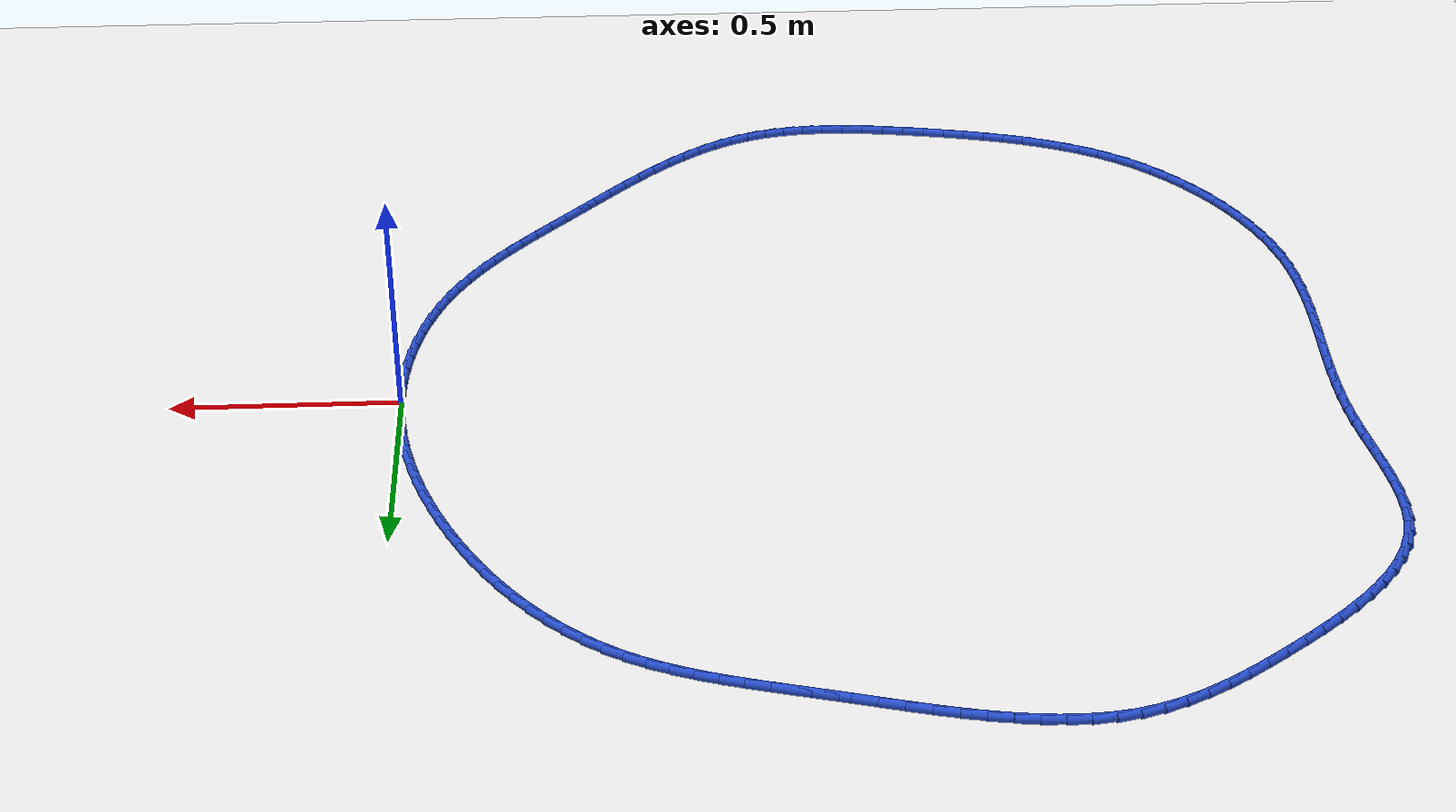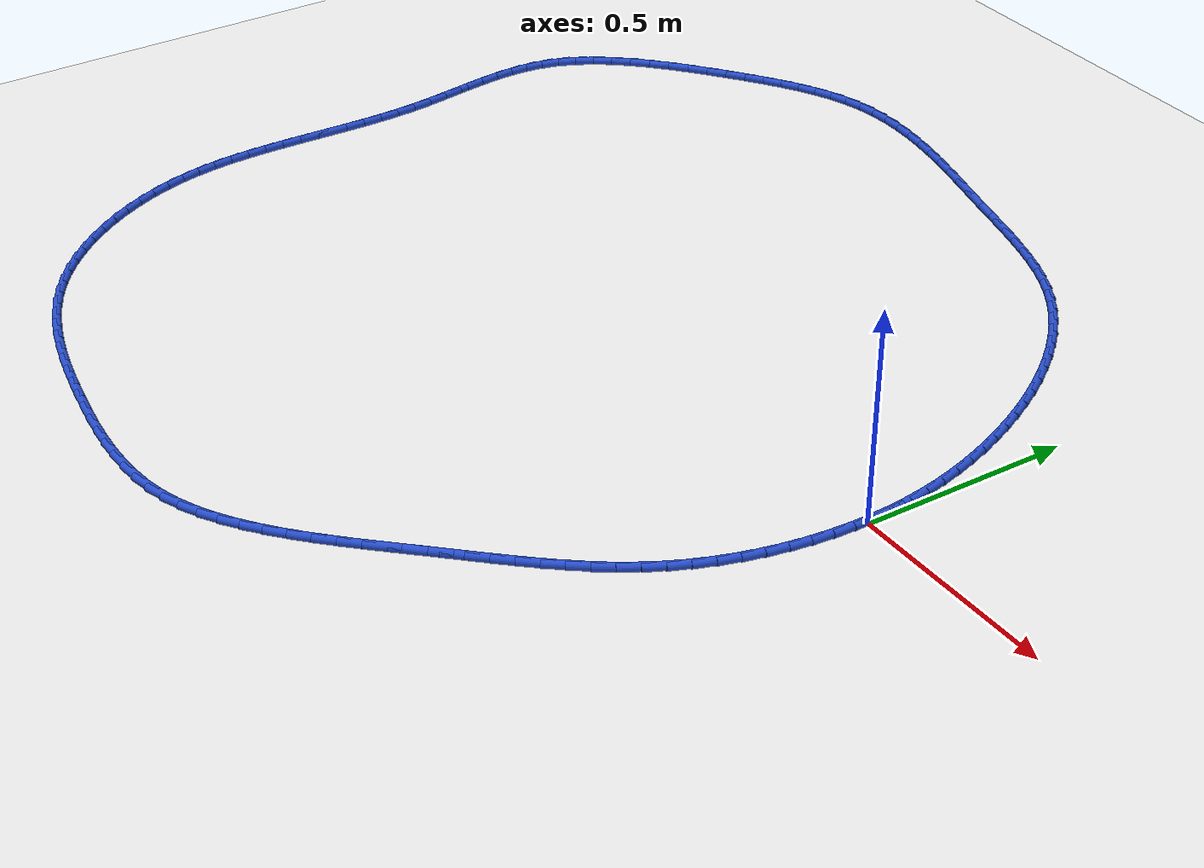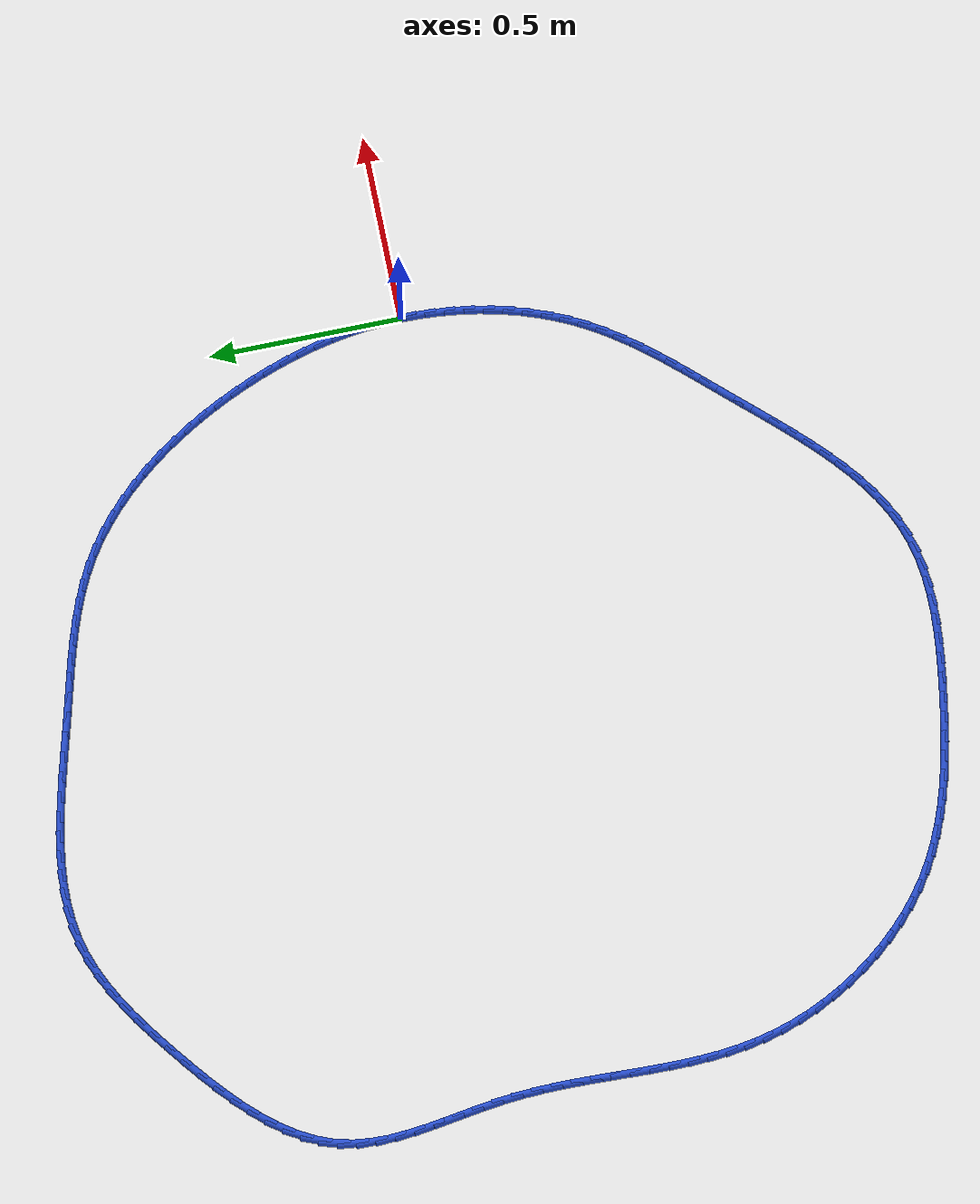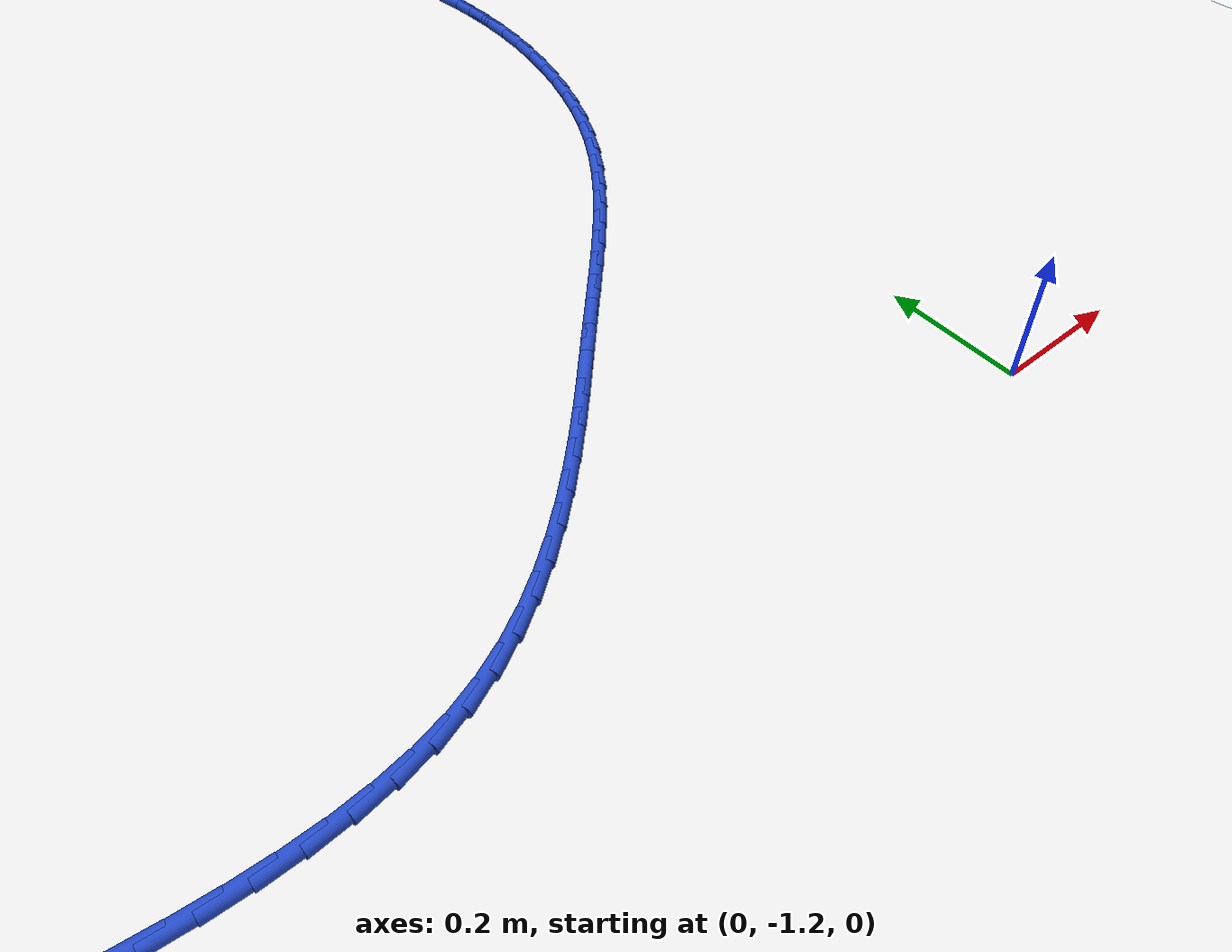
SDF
<sdf version="1.6">
 <world name="default">
  <light name="sun" type="directional">
   <pose>0 0 10 0 -0 0</pose>
   <diffuse>0.8 0.8 0.8 1</diffuse>
   <specular>0.2 0.2 0.2 1</specular>
   <attenuation>
    <range>1000</range>
    <constant>0.9</constant>
    <linear>0.01</linear>
    <quadratic>0.001</quadratic>
   </attenuation>
   <direction>-0.5 0.1 -0.9</direction>
  </light>
  <model name="ground_plane">
   <static>1</static>
   <link name="link">
    <collision name="collision">
     <geometry><plane><normal>0 0 1</normal><size>100 100</size></plane></geometry>
     <surface><friction><ode><mu>100</mu><mu2>50</mu2></ode></friction></surface>
    </collision>
    <visual name="visual">
     <cast_shadows>0</cast_shadows>
     <geometry><plane><normal>0 0 1</normal><size>100 100</size></plane></geometry>
     <material>
      <script><uri>file://media/materials/scripts/gazebo.material</uri><name>Gazebo/WhiteGlow</name></script>
     </material>
    </visual>
   </link>
  </model>
  <gravity>0 0 -9.8</gravity>
  <magnetic_field>6e-06 2.3e-05 -4.2e-05</magnetic_field>
  <atmosphere type="adiabatic"/>
  <physics name="default_physics" default="0" type="ode">
   <max_step_size>0.001</max_step_size>
   <real_time_factor>1</real_time_factor>
   <real_time_update_rate>1000</real_time_update_rate>
  </physics>
  <scene><ambient>0.4 0.4 0.4 1</ambient><background>0.7 0.7 0.7 1</background><shadows>1</shadows></scene>
  <spherical_coordinates>
   <surface_model>EARTH_WGS84</surface_model>
   <latitude_deg>0</latitude_deg>
   <longitude_deg>0</longitude_deg>
   <elevation>0</elevation>
   <heading_deg>0</heading_deg>
  </spherical_coordinates>
  <model name="line">
   <link name="link_0">
    <pose>3.642919299551295e-17 9.71445146547012e-17 0.01 0 1.57 -1.5333083393462763</pose>
    <collision name="collision">
     <geometry><cylinder><radius>0.01</radius><length>0.08</length></cylinder></geometry>
    </collision>
    <visual name="visual">
     <material>
      <script><name>Gazebo/Blue</name><uri>file://media/materials/scripts/gazebo.material</uri></script>
     </material>
     <geometry><cylinder><radius>0.01</radius><length>0.08</length></cylinder></geometry>
    </visual>
   </link>
   <link name="link_1">
    <pose>-0.0018602273220147247 0.0495987099844681 0.01 0 1.57 -1.4833174600700507</pose>
    <collision name="collision">
     <geometry><cylinder><radius>0.01</radius><length>0.08</length></cylinder></geometry>
    </collision>
    <visual name="visual">
     <material>
      <script><name>Gazebo/Blue</name><uri>file://media/materials/scripts/gazebo.material</uri></script>
     </material>
     <geometry><cylinder><radius>0.01</radius><length>0.08</length></cylinder></geometry>
    </visual>
   </link>
   <link name="link_2">
    <pose>-0.006178268365981738 0.09883369557249982 0.01 0 1.57 -1.4345817801698275</pose>
    <collision name="collision">
     <geometry><cylinder><radius>0.01</radius><length>0.08</length></cylinder></geometry>
    </collision>
    <visual name="visual">
     <material>
      <script><name>Gazebo/Blue</name><uri>file://media/materials/scripts/gazebo.material</uri></script>
     </material>
     <geometry><cylinder><radius>0.01</radius><length>0.08</length></cylinder></geometry>
    </visual>
   </link>
   <link name="link_3">
    <pose>-0.01287644401805767 0.14770290668139474 0.01 0 1.57 -1.3873089182403966</pose>
    <collision name="collision">
     <geometry><cylinder><radius>0.01</radius><length>0.08</length></cylinder></geometry>
    </collision>
    <visual name="visual">
     <material>
      <script><name>Gazebo/Blue</name><uri>file://media/materials/scripts/gazebo.material</uri></script>
     </material>
     <geometry><cylinder><radius>0.01</radius><length>0.08</length></cylinder></geometry>
    </visual>
   </link>
   <link name="link_4">
    <pose>-0.021877075164399205 0.1962042932284524 0.01 0 1.57 -1.3416684034358701</pose>
    <collision name="collision">
     <geometry><cylinder><radius>0.01</radius><length>0.08</length></cylinder></geometry>
    </collision>
    <visual name="visual">
     <material>
      <script><name>Gazebo/Blue</name><uri>file://media/materials/scripts/gazebo.material</uri></script>
     </material>
     <geometry><cylinder><radius>0.01</radius><length>0.08</length></cylinder></geometry>
    </visual>
   </link>
   <link name="link_5">
    <pose>-0.03310248269116302 0.2443358051309722 0.01 0 1.57 -1.2977911111290625</pose>
    <collision name="collision">
     <geometry><cylinder><radius>0.01</radius><length>0.08</length></cylinder></geometry>
    </collision>
    <visual name="visual">
     <material>
      <script><name>Gazebo/Blue</name><uri>file://media/materials/scripts/gazebo.material</uri></script>
     </material>
     <geometry><cylinder><radius>0.01</radius><length>0.08</length></cylinder></geometry>
    </visual>
   </link>
   <link name="link_6">
    <pose>-0.04647498748450581 0.29209539230625375 0.01 0 1.57 -1.255770619409367</pose>
    <collision name="collision">
     <geometry><cylinder><radius>0.01</radius><length>0.08</length></cylinder></geometry>
    </collision>
    <visual name="visual">
     <material>
      <script><name>Gazebo/Blue</name><uri>file://media/materials/scripts/gazebo.material</uri></script>
     </material>
     <geometry><cylinder><radius>0.01</radius><length>0.08</length></cylinder></geometry>
    </visual>
   </link>
   <link name="link_7">
    <pose>-0.061916910430584234 0.3394810046715964 0.01 0 1.57 -1.2156660414028329</pose>
    <collision name="collision">
     <geometry><cylinder><radius>0.01</radius><length>0.08</length></cylinder></geometry>
    </collision>
    <visual name="visual">
     <material>
      <script><name>Gazebo/Blue</name><uri>file://media/materials/scripts/gazebo.material</uri></script>
     </material>
     <geometry><cylinder><radius>0.01</radius><length>0.08</length></cylinder></geometry>
    </visual>
   </link>
   <link name="link_8">
    <pose>-0.07935057241555499 0.38649059214429987 0.01 0 1.57 -1.1775058526492614</pose>
    <collision name="collision">
     <geometry><cylinder><radius>0.01</radius><length>0.08</length></cylinder></geometry>
    </collision>
    <visual name="visual">
     <material>
      <script><name>Gazebo/Blue</name><uri>file://media/materials/scripts/gazebo.material</uri></script>
     </material>
     <geometry><cylinder><radius>0.01</radius><length>0.08</length></cylinder></geometry>
    </visual>
   </link>
   <link name="link_9">
    <pose>-0.09869829432557475 0.43312210464166345 0.01 0 1.57 -1.1408050658484743</pose>
    <collision name="collision">
     <geometry><cylinder><radius>0.01</radius><length>0.08</length></cylinder></geometry>
    </collision>
    <visual name="visual">
     <material>
      <script><name>Gazebo/Blue</name><uri>file://media/materials/scripts/gazebo.material</uri></script>
     </material>
     <geometry><cylinder><radius>0.01</radius><length>0.08</length></cylinder></geometry>
    </visual>
   </link>
   <link name="link_10">
    <pose>-0.11989256357617334 0.4793362051244956 0.01 0 1.57 -1.103372057153485</pose>
    <collision name="collision">
     <geometry><cylinder><radius>0.01</radius><length>0.08</length></cylinder></geometry>
    </collision>
    <visual name="visual">
     <material>
      <script><name>Gazebo/Blue</name><uri>file://media/materials/scripts/gazebo.material</uri></script>
     </material>
     <geometry><cylinder><radius>0.01</radius><length>0.08</length></cylinder></geometry>
    </visual>
   </link>
   <link name="link_11">
    <pose>-0.1429085849492884 0.5249368855281061 0.01 0 1.57 -1.064329445693956</pose>
    <collision name="collision">
     <geometry><cylinder><radius>0.01</radius><length>0.08</length></cylinder></geometry>
    </collision>
    <visual name="visual">
     <material>
      <script><name>Gazebo/Blue</name><uri>file://media/materials/scripts/gazebo.material</uri></script>
     </material>
     <geometry><cylinder><radius>0.01</radius><length>0.08</length></cylinder></geometry>
    </visual>
   </link>
   <link name="link_12">
    <pose>-0.16773278098538216 0.5696869953232829 0.01 0 1.57 -1.0233111332169653</pose>
    <collision name="collision">
     <geometry><cylinder><radius>0.01</radius><length>0.08</length></cylinder></geometry>
    </collision>
    <visual name="visual">
     <material>
      <script><name>Gazebo/Blue</name><uri>file://media/materials/scripts/gazebo.material</uri></script>
     </material>
     <geometry><cylinder><radius>0.01</radius><length>0.08</length></cylinder></geometry>
    </visual>
   </link>
   <link name="link_13">
    <pose>-0.19435157427204944 0.6133493838079518 0.01 0 1.57 -0.9799407837961018</pose>
    <collision name="collision">
     <geometry><cylinder><radius>0.01</radius><length>0.08</length></cylinder></geometry>
    </collision>
    <visual name="visual">
     <material>
      <script><name>Gazebo/Blue</name><uri>file://media/materials/scripts/gazebo.material</uri></script>
     </material>
     <geometry><cylinder><radius>0.01</radius><length>0.08</length></cylinder></geometry>
    </visual>
   </link>
   <link name="link_14">
    <pose>-0.2227513873968846 0.6556869002800372 0.01 0 1.57 -0.9338307504049684</pose>
    <collision name="collision">
     <geometry><cylinder><radius>0.01</radius><length>0.08</length></cylinder></geometry>
    </collision>
    <visual name="visual">
     <material>
      <script><name>Gazebo/Blue</name><uri>file://media/materials/scripts/gazebo.material</uri></script>
     </material>
     <geometry><cylinder><radius>0.01</radius><length>0.08</length></cylinder></geometry>
    </visual>
   </link>
   <link name="link_15">
    <pose>-0.25291864294748256 0.6964623940374646 0.01 0 1.57 -0.884584373394327</pose>
    <collision name="collision">
     <geometry><cylinder><radius>0.01</radius><length>0.08</length></cylinder></geometry>
    </collision>
    <visual name="visual">
     <material>
      <script><name>Gazebo/Blue</name><uri>file://media/materials/scripts/gazebo.material</uri></script>
     </material>
     <geometry><cylinder><radius>0.01</radius><length>0.08</length></cylinder></geometry>
    </visual>
   </link>
   <link name="link_16">
    <pose>-0.2848397635114379 0.7354387143781587 0.01 0 1.57 -0.8318028260945439</pose>
    <collision name="collision">
     <geometry><cylinder><radius>0.01</radius><length>0.08</length></cylinder></geometry>
    </collision>
    <visual name="visual">
     <material>
      <script><name>Gazebo/Blue</name><uri>file://media/materials/scripts/gazebo.material</uri></script>
     </material>
     <geometry><cylinder><radius>0.01</radius><length>0.08</length></cylinder></geometry>
    </visual>
   </link>
   <link name="link_17">
    <pose>-0.3185011716763452 0.7723787106000445 0.01 0 1.57 -0.7750980400064106</pose>
    <collision name="collision">
     <geometry><cylinder><radius>0.01</radius><length>0.08</length></cylinder></geometry>
    </collision>
    <visual name="visual">
     <material>
      <script><name>Gazebo/Blue</name><uri>file://media/materials/scripts/gazebo.material</uri></script>
     </material>
     <geometry><cylinder><radius>0.01</radius><length>0.08</length></cylinder></geometry>
    </visual>
   </link>
   <link name="link_18">
    <pose>-0.353889290029799 0.8070452320010473 0.01 0 1.57 -0.7141134512572678</pose>
    <collision name="collision">
     <geometry><cylinder><radius>0.01</radius><length>0.08</length></cylinder></geometry>
    </collision>
    <visual name="visual">
     <material>
      <script><name>Gazebo/Blue</name><uri>file://media/materials/scripts/gazebo.material</uri></script>
     </material>
     <geometry><cylinder><radius>0.01</radius><length>0.08</length></cylinder></geometry>
    </visual>
   </link>
   <link name="link_19">
    <pose>-0.39099054115939424 0.8392011278790923 0.01 0 1.57 -0.6485541460785554</pose>
    <collision name="collision">
     <geometry><cylinder><radius>0.01</radius><length>0.08</length></cylinder></geometry>
    </collision>
    <visual name="visual">
     <material>
      <script><name>Gazebo/Blue</name><uri>file://media/materials/scripts/gazebo.material</uri></script>
     </material>
     <geometry><cylinder><radius>0.01</radius><length>0.08</length></cylinder></geometry>
    </visual>
   </link>
   <link name="link_20">
    <pose>-0.4297913476527252 0.868609247532104 0.01 0 1.57 -0.5782270983372392</pose>
    <collision name="collision">
     <geometry><cylinder><radius>0.01</radius><length>0.08</length></cylinder></geometry>
    </collision>
    <visual name="visual">
     <material>
      <script><name>Gazebo/Blue</name><uri>file://media/materials/scripts/gazebo.material</uri></script>
     </material>
     <geometry><cylinder><radius>0.01</radius><length>0.08</length></cylinder></geometry>
    </visual>
   </link>
   <link name="link_21">
    <pose>-0.47027813209738667 0.895032440258008 0.01 0 1.57 -0.5046716805952203</pose>
    <collision name="collision">
     <geometry><cylinder><radius>0.01</radius><length>0.08</length></cylinder></geometry>
    </collision>
    <visual name="visual">
     <material>
      <script><name>Gazebo/Blue</name><uri>file://media/materials/scripts/gazebo.material</uri></script>
     </material>
     <geometry><cylinder><radius>0.01</radius><length>0.08</length></cylinder></geometry>
    </visual>
   </link>
   <link name="link_22">
    <pose>-0.5124206097216926 0.9183112698539777 0.01 0 1.57 -0.43753297119028606</pose>
    <collision name="collision">
     <geometry><cylinder><radius>0.01</radius><length>0.08</length></cylinder></geometry>
    </collision>
    <visual name="visual">
     <material>
      <script><name>Gazebo/Blue</name><uri>file://media/materials/scripts/gazebo.material</uri></script>
     </material>
     <geometry><cylinder><radius>0.01</radius><length>0.08</length></cylinder></geometry>
    </visual>
   </link>
   <link name="link_23">
    <pose>-0.5560911612301642 0.938739052922039 0.01 0 1.57 -0.3808743160083158</pose>
    <collision name="collision">
     <geometry><cylinder><radius>0.01</radius><length>0.08</length></cylinder></geometry>
    </collision>
    <visual name="visual">
     <material>
      <script><name>Gazebo/Blue</name><uri>file://media/materials/scripts/gazebo.material</uri></script>
     </material>
     <geometry><cylinder><radius>0.01</radius><length>0.08</length></cylinder></geometry>
    </visual>
   </link>
   <link name="link_24">
    <pose>-0.6011270147227181 0.9567726188622772 0.01 0 1.57 -0.33499728040956245</pose>
    <collision name="collision">
     <geometry><cylinder><radius>0.01</radius><length>0.08</length></cylinder></geometry>
    </collision>
    <visual name="visual">
     <material>
      <script><name>Gazebo/Blue</name><uri>file://media/materials/scripts/gazebo.material</uri></script>
     </material>
     <geometry><cylinder><radius>0.01</radius><length>0.08</length></cylinder></geometry>
    </visual>
   </link>
   <link name="link_25">
    <pose>-0.647365350607999 0.9728690189113463 0.01 0 1.57 -0.2998356464150374</pose>
    <collision name="collision">
     <geometry><cylinder><radius>0.01</radius><length>0.08</length></cylinder></geometry>
    </collision>
    <visual name="visual">
     <material>
      <script><name>Gazebo/Blue</name><uri>file://media/materials/scripts/gazebo.material</uri></script>
     </material>
     <geometry><cylinder><radius>0.01</radius><length>0.08</length></cylinder></geometry>
    </visual>
   </link>
   <link name="link_26">
    <pose>-0.6946433492946515 0.9874853043059003 0.01 0 1.57 -0.2751231004270388</pose>
    <collision name="collision">
     <geometry><cylinder><radius>0.01</radius><length>0.08</length></cylinder></geometry>
    </collision>
    <visual name="visual">
     <material>
      <script><name>Gazebo/Blue</name><uri>file://media/materials/scripts/gazebo.material</uri></script>
     </material>
     <geometry><cylinder><radius>0.01</radius><length>0.08</length></cylinder></geometry>
    </visual>
   </link>
   <link name="link_27">
    <pose>-0.7427981911913211 1.0010785262825939 0.01 0 1.57 -0.2605166554803643</pose>
    <collision name="collision">
     <geometry><cylinder><radius>0.01</radius><length>0.08</length></cylinder></geometry>
    </collision>
    <visual name="visual">
     <material>
      <script><name>Gazebo/Blue</name><uri>file://media/materials/scripts/gazebo.material</uri></script>
     </material>
     <geometry><cylinder><radius>0.01</radius><length>0.08</length></cylinder></geometry>
    </visual>
   </link>
   <link name="link_28">
    <pose>-0.7916670567066526 1.0141057360780807 0.01 0 1.57 -0.25567598355072313</pose>
    <collision name="collision">
     <geometry><cylinder><radius>0.01</radius><length>0.08</length></cylinder></geometry>
    </collision>
    <visual name="visual">
     <material>
      <script><name>Gazebo/Blue</name><uri>file://media/materials/scripts/gazebo.material</uri></script>
     </material>
     <geometry><cylinder><radius>0.01</radius><length>0.08</length></cylinder></geometry>
    </visual>
   </link>
   <link name="link_29">
    <pose>-0.8410871262492906 1.0270239849290153 0.01 0 1.57 -0.2600022977419969</pose>
    <collision name="collision">
     <geometry><cylinder><radius>0.01</radius><length>0.08</length></cylinder></geometry>
    </collision>
    <visual name="visual">
     <material>
      <script><name>Gazebo/Blue</name><uri>file://media/materials/scripts/gazebo.material</uri></script>
     </material>
     <geometry><cylinder><radius>0.01</radius><length>0.08</length></cylinder></geometry>
    </visual>
   </link>
   <link name="link_30">
    <pose>-0.8908964800127943 1.0402744685579586 0.01 0 1.57 -0.2654009326328046</pose>
    <collision name="collision">
     <geometry><cylinder><radius>0.01</radius><length>0.08</length></cylinder></geometry>
    </collision>
    <visual name="visual">
     <material>
      <script><name>Gazebo/Blue</name><uri>file://media/materials/scripts/gazebo.material</uri></script>
     </material>
     <geometry><cylinder><radius>0.01</radius><length>0.08</length></cylinder></geometry>
    </visual>
   </link>
   <link name="link_31">
    <pose>-0.9409568540531428 1.0538815321112391 0.01 0 1.57 -0.2634574509383754</pose>
    <collision name="collision">
     <geometry><cylinder><radius>0.01</radius><length>0.08</length></cylinder></geometry>
    </collision>
    <visual name="visual">
     <material>
      <script><name>Gazebo/Blue</name><uri>file://media/materials/scripts/gazebo.material</uri></script>
     </material>
     <geometry><cylinder><radius>0.01</radius><length>0.08</length></cylinder></geometry>
    </visual>
   </link>
   <link name="link_32">
    <pose>-0.9911554123877682 1.0674214432059488 0.01 0 1.57 -0.2537781394267379</pose>
    <collision name="collision">
     <geometry><cylinder><radius>0.01</radius><length>0.08</length></cylinder></geometry>
    </collision>
    <visual name="visual">
     <material>
      <script><name>Gazebo/Blue</name><uri>file://media/materials/scripts/gazebo.material</uri></script>
     </material>
     <geometry><cylinder><radius>0.01</radius><length>0.08</length></cylinder></geometry>
    </visual>
   </link>
   <link name="link_33">
    <pose>-1.041380573818708 1.0804483583361006 0.01 0 1.57 -0.23619418724445662</pose>
    <collision name="collision">
     <geometry><cylinder><radius>0.01</radius><length>0.08</length></cylinder></geometry>
    </collision>
    <visual name="visual">
     <material>
      <script><name>Gazebo/Blue</name><uri>file://media/materials/scripts/gazebo.material</uri></script>
     </material>
     <geometry><cylinder><radius>0.01</radius><length>0.08</length></cylinder></geometry>
    </visual>
   </link>
   <link name="link_34">
    <pose>-1.0915207571480003 1.0925164339957065 0.01 0 1.57 -0.21035020720188574</pose>
    <collision name="collision">
     <geometry><cylinder><radius>0.01</radius><length>0.08</length></cylinder></geometry>
    </collision>
    <visual name="visual">
     <material>
      <script><name>Gazebo/Blue</name><uri>file://media/materials/scripts/gazebo.material</uri></script>
     </material>
     <geometry><cylinder><radius>0.01</radius><length>0.08</length></cylinder></geometry>
    </visual>
   </link>
   <link name="link_35">
    <pose>-1.1414643811776826 1.1031798266787785 0.01 0 1.57 -0.1757204989856719</pose>
    <collision name="collision">
     <geometry><cylinder><radius>0.01</radius><length>0.08</length></cylinder></geometry>
    </collision>
    <visual name="visual">
     <material>
      <script><name>Gazebo/Blue</name><uri>file://media/materials/scripts/gazebo.material</uri></script>
     </material>
     <geometry><cylinder><radius>0.01</radius><length>0.08</length></cylinder></geometry>
    </visual>
   </link>
   <link name="link_36">
    <pose>-1.1910998647097921 1.1119926928793287 0.01 0 1.57 -0.13164096641273396</pose>
    <collision name="collision">
     <geometry><cylinder><radius>0.01</radius><length>0.08</length></cylinder></geometry>
    </collision>
    <visual name="visual">
     <material>
      <script><name>Gazebo/Blue</name><uri>file://media/materials/scripts/gazebo.material</uri></script>
     </material>
     <geometry><cylinder><radius>0.01</radius><length>0.08</length></cylinder></geometry>
    </visual>
   </link>
   <link name="link_37">
    <pose>-1.240315626546367 1.1185091890913694 0.01 0 1.57 -0.07737065513932036</pose>
    <collision name="collision">
     <geometry><cylinder><radius>0.01</radius><length>0.08</length></cylinder></geometry>
    </collision>
    <visual name="visual">
     <material>
      <script><name>Gazebo/Blue</name><uri>file://media/materials/scripts/gazebo.material</uri></script>
     </material>
     <geometry><cylinder><radius>0.01</radius><length>0.08</length></cylinder></geometry>
    </visual>
   </link>
   <link name="link_38">
    <pose>-1.2890000854894446 1.1222834718089127 0.01 0 1.57 -0.012201861098301658</pose>
    <collision name="collision">
     <geometry><cylinder><radius>0.01</radius><length>0.08</length></cylinder></geometry>
    </collision>
    <visual name="visual">
     <material>
      <script><name>Gazebo/Blue</name><uri>file://media/materials/scripts/gazebo.material</uri></script>
     </material>
     <geometry><cylinder><radius>0.01</radius><length>0.08</length></cylinder></geometry>
    </visual>
   </link>
   <link name="link_39">
    <pose>-1.3370416603410629 1.1228696975259709 0.01 0 1.57 0.0643614175976423</pose>
    <collision name="collision">
     <geometry><cylinder><radius>0.01</radius><length>0.08</length></cylinder></geometry>
    </collision>
    <visual name="visual">
     <material>
      <script><name>Gazebo/Blue</name><uri>file://media/materials/scripts/gazebo.material</uri></script>
     </material>
     <geometry><cylinder><radius>0.01</radius><length>0.08</length></cylinder></geometry>
    </visual>
   </link>
   <link name="link_40">
    <pose>-1.3843287699032587 1.1198220227365556 0.01 0 1.57 0.15234874056052025</pose>
    <collision name="collision">
     <geometry><cylinder><radius>0.01</radius><length>0.08</length></cylinder></geometry>
    </collision>
    <visual name="visual">
     <material>
      <script><name>Gazebo/Blue</name><uri>file://media/materials/scripts/gazebo.material</uri></script>
     </material>
     <geometry><cylinder><radius>0.01</radius><length>0.08</length></cylinder></geometry>
    </visual>
   </link>
   <link name="link_41">
    <pose>-1.4307498329780703 1.1126946039346794 0.01 0 1.57 0.2505308959512029</pose>
    <collision name="collision">
     <geometry><cylinder><radius>0.01</radius><length>0.08</length></cylinder></geometry>
    </collision>
    <visual name="visual">
     <material>
      <script><name>Gazebo/Blue</name><uri>file://media/materials/scripts/gazebo.material</uri></script>
     </material>
     <geometry><cylinder><radius>0.01</radius><length>0.08</length></cylinder></geometry>
    </visual>
   </link>
   <link name="link_42">
    <pose>-1.4761991969471224 1.101063770459122 0.01 0 1.57 0.3467858972259525</pose>
    <collision name="collision">
     <geometry><cylinder><radius>0.01</radius><length>0.08</length></cylinder></geometry>
    </collision>
    <visual name="visual">
     <material>
      <script><name>Gazebo/Blue</name><uri>file://media/materials/scripts/gazebo.material</uri></script>
     </material>
     <geometry><cylinder><radius>0.01</radius><length>0.08</length></cylinder></geometry>
    </visual>
   </link>
   <link name="link_43">
    <pose>-1.5206985565593427 1.0849821298810909 0.01 0 1.57 0.4296740758856446</pose>
    <collision name="collision">
     <geometry><cylinder><radius>0.01</radius><length>0.08</length></cylinder></geometry>
    </collision>
    <visual name="visual">
     <material>
      <script><name>Gazebo/Blue</name><uri>file://media/materials/scripts/gazebo.material</uri></script>
     </material>
     <geometry><cylinder><radius>0.01</radius><length>0.08</length></cylinder></geometry>
    </visual>
   </link>
   <link name="link_44">
    <pose>-1.5643921408374286 1.0649605670692253 0.01 0 1.57 0.4985817375653926</pose>
    <collision name="collision">
     <geometry><cylinder><radius>0.01</radius><length>0.08</length></cylinder></geometry>
    </collision>
    <visual name="visual">
     <material>
      <script><name>Gazebo/Blue</name><uri>file://media/materials/scripts/gazebo.material</uri></script>
     </material>
     <geometry><cylinder><radius>0.01</radius><length>0.08</length></cylinder></geometry>
    </visual>
   </link>
   <link name="link_45">
    <pose>-1.607429144317001 1.0415285378745829 0.01 0 1.57 0.5540555599129547</pose>
    <collision name="collision">
     <geometry><cylinder><radius>0.01</radius><length>0.08</length></cylinder></geometry>
    </collision>
    <visual name="visual">
     <material>
      <script><name>Gazebo/Blue</name><uri>file://media/materials/scripts/gazebo.material</uri></script>
     </material>
     <geometry><cylinder><radius>0.01</radius><length>0.08</length></cylinder></geometry>
    </visual>
   </link>
   <link name="link_46">
    <pose>-1.6499587615336824 1.0152154981482209 0.01 0 1.57 0.5969824596638393</pose>
    <collision name="collision">
     <geometry><cylinder><radius>0.01</radius><length>0.08</length></cylinder></geometry>
    </collision>
    <visual name="visual">
     <material>
      <script><name>Gazebo/Blue</name><uri>file://media/materials/scripts/gazebo.material</uri></script>
     </material>
     <geometry><cylinder><radius>0.01</radius><length>0.08</length></cylinder></geometry>
    </visual>
   </link>
   <link name="link_47">
    <pose>-1.6921301870230945 0.9865509037411971 0.01 0 1.57 0.6283061228027785</pose>
    <collision name="collision">
     <geometry><cylinder><radius>0.01</radius><length>0.08</length></cylinder></geometry>
    </collision>
    <visual name="visual">
     <material>
      <script><name>Gazebo/Blue</name><uri>file://media/materials/scripts/gazebo.material</uri></script>
     </material>
     <geometry><cylinder><radius>0.01</radius><length>0.08</length></cylinder></geometry>
    </visual>
   </link>
   <link name="link_48">
    <pose>-1.7340926153208596 0.9560642105045684 0.01 0 1.57 0.6488808542251842</pose>
    <collision name="collision">
     <geometry><cylinder><radius>0.01</radius><length>0.08</length></cylinder></geometry>
    </collision>
    <visual name="visual">
     <material>
      <script><name>Gazebo/Blue</name><uri>file://media/materials/scripts/gazebo.material</uri></script>
     </material>
     <geometry><cylinder><radius>0.01</radius><length>0.08</length></cylinder></geometry>
    </visual>
   </link>
   <link name="link_49">
    <pose>-1.775994390227799 0.9242842288722098 0.01 0 1.57 0.6644556283217632</pose>
    <collision name="collision">
     <geometry><cylinder><radius>0.01</radius><length>0.08</length></cylinder></geometry>
    </collision>
    <visual name="visual">
     <material>
      <script><name>Gazebo/Blue</name><uri>file://media/materials/scripts/gazebo.material</uri></script>
     </material>
     <geometry><cylinder><radius>0.01</radius><length>0.08</length></cylinder></geometry>
    </visual>
   </link>
   <link name="link_50">
    <pose>-1.817760373162467 0.8915702224701834 0.01 0 1.57 0.6873590482464818</pose>
    <collision name="collision">
     <geometry><cylinder><radius>0.01</radius><length>0.08</length></cylinder></geometry>
    </collision>
    <visual name="visual">
     <material>
      <script><name>Gazebo/Blue</name><uri>file://media/materials/scripts/gazebo.material</uri></script>
     </material>
     <geometry><cylinder><radius>0.01</radius><length>0.08</length></cylinder></geometry>
    </visual>
   </link>
   <link name="link_51">
    <pose>-1.8587937516257595 0.8578856825752517 0.01 0 1.57 0.7198580936257576</pose>
    <collision name="collision">
     <geometry><cylinder><radius>0.01</radius><length>0.08</length></cylinder></geometry>
    </collision>
    <visual name="visual">
     <material>
      <script><name>Gazebo/Blue</name><uri>file://media/materials/scripts/gazebo.material</uri></script>
     </material>
     <geometry><cylinder><radius>0.01</radius><length>0.08</length></cylinder></geometry>
    </visual>
   </link>
   <link name="link_52">
    <pose>-1.898423410027241 0.8231377297927263 0.01 0 1.57 0.7629325911958803</pose>
    <collision name="collision">
     <geometry><cylinder><radius>0.01</radius><length>0.08</length></cylinder></geometry>
    </collision>
    <visual name="visual">
     <material>
      <script><name>Gazebo/Blue</name><uri>file://media/materials/scripts/gazebo.material</uri></script>
     </material>
     <geometry><cylinder><radius>0.01</radius><length>0.08</length></cylinder></geometry>
    </visual>
   </link>
   <link name="link_53">
    <pose>-1.9359782327764772 0.78723348472792 0.01 0 1.57 0.8179668360479697</pose>
    <collision name="collision">
     <geometry><cylinder><radius>0.01</radius><length>0.08</length></cylinder></geometry>
    </collision>
    <visual name="visual">
     <material>
      <script><name>Gazebo/Blue</name><uri>file://media/materials/scripts/gazebo.material</uri></script>
     </material>
     <geometry><cylinder><radius>0.01</radius><length>0.08</length></cylinder></geometry>
    </visual>
   </link>
   <link name="link_54">
    <pose>-1.9707871042830318 0.7500800679861436 0.01 0 1.57 0.8866948560286647</pose>
    <collision name="collision">
     <geometry><cylinder><radius>0.01</radius><length>0.08</length></cylinder></geometry>
    </collision>
    <visual name="visual">
     <material>
      <script><name>Gazebo/Blue</name><uri>file://media/materials/scripts/gazebo.material</uri></script>
     </material>
     <geometry><cylinder><radius>0.01</radius><length>0.08</length></cylinder></geometry>
    </visual>
   </link>
   <link name="link_55">
    <pose>-2.002178908956471 0.7115846001727095 0.01 0 1.57 0.9710391698354408</pose>
    <collision name="collision">
     <geometry><cylinder><radius>0.01</radius><length>0.08</length></cylinder></geometry>
    </collision>
    <visual name="visual">
     <material>
      <script><name>Gazebo/Blue</name><uri>file://media/materials/scripts/gazebo.material</uri></script>
     </material>
     <geometry><cylinder><radius>0.01</radius><length>0.08</length></cylinder></geometry>
    </visual>
   </link>
   <link name="link_56">
    <pose>-2.0294825312063596 0.6716542018929303 0.01 0 1.57 1.0727377393904476</pose>
    <collision name="collision">
     <geometry><cylinder><radius>0.01</radius><length>0.08</length></cylinder></geometry>
    </collision>
    <visual name="visual">
     <material>
      <script><name>Gazebo/Blue</name><uri>file://media/materials/scripts/gazebo.material</uri></script>
     </material>
     <geometry><cylinder><radius>0.01</radius><length>0.08</length></cylinder></geometry>
    </visual>
   </link>
   <link name="link_57">
    <pose>-2.052026855442261 0.6301959937521165 0.01 0 1.57 1.1926464720259444</pose>
    <collision name="collision">
     <geometry><cylinder><radius>0.01</radius><length>0.08</length></cylinder></geometry>
    </collision>
    <visual name="visual">
     <material>
      <script><name>Gazebo/Blue</name><uri>file://media/materials/scripts/gazebo.material</uri></script>
     </material>
     <geometry><cylinder><radius>0.01</radius><length>0.08</length></cylinder></geometry>
    </visual>
   </link>
   <link name="link_58">
    <pose>-2.0691407660737413 0.5871170963555814 0.01 0 1.57 1.3284170155489716</pose>
    <collision name="collision">
     <geometry><cylinder><radius>0.01</radius><length>0.08</length></cylinder></geometry>
    </collision>
    <visual name="visual">
     <material>
      <script><name>Gazebo/Blue</name><uri>file://media/materials/scripts/gazebo.material</uri></script>
     </material>
     <geometry><cylinder><radius>0.01</radius><length>0.08</length></cylinder></geometry>
    </visual>
   </link>
   <link name="link_59">
    <pose>-2.0802124267342177 0.5423360668450955 0.01 0 1.57 1.4564839817098578</pose>
    <collision name="collision">
     <geometry><cylinder><radius>0.01</radius><length>0.08</length></cylinder></geometry>
    </collision>
    <visual name="visual">
     <material>
      <script><name>Gazebo/Blue</name><uri>file://media/materials/scripts/gazebo.material</uri></script>
     </material>
     <geometry><cylinder><radius>0.01</radius><length>0.08</length></cylinder></geometry>
    </visual>
   </link>
   <link name="link_60">
    <pose>-2.085538518990908 0.49594673959784213 0.01 0 1.57 1.5584921550619775</pose>
    <collision name="collision">
     <geometry><cylinder><radius>0.01</radius><length>0.08</length></cylinder></geometry>
    </collision>
    <visual name="visual">
     <material>
      <script><name>Gazebo/Blue</name><uri>file://media/materials/scripts/gazebo.material</uri></script>
     </material>
     <geometry><cylinder><radius>0.01</radius><length>0.08</length></cylinder></geometry>
    </visual>
   </link>
   <link name="link_61">
    <pose>-2.0861262784041963 0.44818003372527043 0.01 0 1.57 -1.5070017228179915</pose>
    <collision name="collision">
     <geometry><cylinder><radius>0.01</radius><length>0.08</length></cylinder></geometry>
    </collision>
    <visual name="visual">
     <material>
      <script><name>Gazebo/Blue</name><uri>file://media/materials/scripts/gazebo.material</uri></script>
     </material>
     <geometry><cylinder><radius>0.01</radius><length>0.08</length></cylinder></geometry>
    </visual>
   </link>
   <link name="link_62">
    <pose>-2.083001875773323 0.39927052144923797 0.01 0 1.57 -1.454687901687123</pose>
    <collision name="collision">
     <geometry><cylinder><radius>0.01</radius><length>0.08</length></cylinder></geometry>
    </collision>
    <visual name="visual">
     <material>
      <script><name>Gazebo/Blue</name><uri>file://media/materials/scripts/gazebo.material</uri></script>
     </material>
     <geometry><cylinder><radius>0.01</radius><length>0.08</length></cylinder></geometry>
    </visual>
   </link>
   <link name="link_63">
    <pose>-2.07719148189753 0.3494527749916009 0.01 0 1.57 -1.4239116671337897</pose>
    <collision name="collision">
     <geometry><cylinder><radius>0.01</radius><length>0.08</length></cylinder></geometry>
    </collision>
    <visual name="visual">
     <material>
      <script><name>Gazebo/Blue</name><uri>file://media/materials/scripts/gazebo.material</uri></script>
     </material>
     <geometry><cylinder><radius>0.01</radius><length>0.08</length></cylinder></geometry>
    </visual>
   </link>
   <link name="link_64">
    <pose>-2.069721267576058 0.2989613665742165 0.01 0 1.57 -1.4130029870904939</pose>
    <collision name="collision">
     <geometry><cylinder><radius>0.01</radius><length>0.08</length></cylinder></geometry>
    </collision>
    <visual name="visual">
     <material>
      <script><name>Gazebo/Blue</name><uri>file://media/materials/scripts/gazebo.material</uri></script>
     </material>
     <geometry><cylinder><radius>0.01</radius><length>0.08</length></cylinder></geometry>
    </visual>
   </link>
   <link name="link_65">
    <pose>-2.0616174036081483 0.24803086841894134 0.01 0 1.57 -1.4211205863632141</pose>
    <collision name="collision">
     <geometry><cylinder><radius>0.01</radius><length>0.08</length></cylinder></geometry>
    </collision>
    <visual name="visual">
     <material>
      <script><name>Gazebo/Blue</name><uri>file://media/materials/scripts/gazebo.material</uri></script>
     </material>
     <geometry><cylinder><radius>0.01</radius><length>0.08</length></cylinder></geometry>
    </visual>
   </link>
   <link name="link_66">
    <pose>-2.0539060607930426 0.19689585274763197 0.01 0 1.57 -1.4482811145953538</pose>
    <collision name="collision">
     <geometry><cylinder><radius>0.01</radius><length>0.08</length></cylinder></geometry>
    </collision>
    <visual name="visual">
     <material>
      <script><name>Gazebo/Blue</name><uri>file://media/materials/scripts/gazebo.material</uri></script>
     </material>
     <geometry><cylinder><radius>0.01</radius><length>0.08</length></cylinder></geometry>
    </visual>
   </link>
   <link name="link_67">
    <pose>-2.0476134099234784 0.14579089178108068 0.01 0 1.57 -1.490536856622085</pose>
    <collision name="collision">
     <geometry><cylinder><radius>0.01</radius><length>0.08</length></cylinder></geometry>
    </collision>
    <visual name="visual">
     <material>
      <script><name>Gazebo/Blue</name><uri>file://media/materials/scripts/gazebo.material</uri></script>
     </material>
     <geometry><cylinder><radius>0.01</radius><length>0.08</length></cylinder></geometry>
    </visual>
   </link>
   <link name="link_68">
    <pose>-2.043520984564976 0.09491048674120858 0.01 0 1.57 -1.5297198922819308</pose>
    <collision name="collision">
     <geometry><cylinder><radius>0.01</radius><length>0.08</length></cylinder></geometry>
    </collision>
    <visual name="visual">
     <material>
      <script><name>Gazebo/Blue</name><uri>file://media/materials/scripts/gazebo.material</uri></script>
     </material>
     <geometry><cylinder><radius>0.01</radius><length>0.08</length></cylinder></geometry>
    </visual>
   </link>
   <link name="link_69">
    <pose>-2.041440517036531 0.044290287700851624 0.01 0 1.57 -1.5609272316955507</pose>
    <collision name="collision">
     <geometry><cylinder><radius>0.01</radius><length>0.08</length></cylinder></geometry>
    </collision>
    <visual name="visual">
     <material>
      <script><name>Gazebo/Blue</name><uri>file://media/materials/scripts/gazebo.material</uri></script>
     </material>
     <geometry><cylinder><radius>0.01</radius><length>0.08</length></cylinder></geometry>
    </visual>
   </link>
   <link name="link_70">
    <pose>-2.0409434567465357 -0.006073413039268928 0.01 0 1.57 1.5576702714785604</pose>
    <collision name="collision">
     <geometry><cylinder><radius>0.01</radius><length>0.08</length></cylinder></geometry>
    </collision>
    <visual name="visual">
     <material>
      <script><name>Gazebo/Blue</name><uri>file://media/materials/scripts/gazebo.material</uri></script>
     </material>
     <geometry><cylinder><radius>0.01</radius><length>0.08</length></cylinder></geometry>
    </visual>
   </link>
   <link name="link_71">
    <pose>-2.0416012531033827 -0.05618432317843016 0.01 0 1.57 1.5430446949970251</pose>
    <collision name="collision">
     <geometry><cylinder><radius>0.01</radius><length>0.08</length></cylinder></geometry>
    </collision>
    <visual name="visual">
     <material>
      <script><name>Gazebo/Blue</name><uri>file://media/materials/scripts/gazebo.material</uri></script>
     </material>
     <geometry><cylinder><radius>0.01</radius><length>0.08</length></cylinder></geometry>
    </visual>
   </link>
   <link name="link_72">
    <pose>-2.042985355515464 -0.10604615041591037 0.01 0 1.57 1.536912119272726</pose>
    <collision name="collision">
     <geometry><cylinder><radius>0.01</radius><length>0.08</length></cylinder></geometry>
    </collision>
    <visual name="visual">
     <material>
      <script><name>Gazebo/Blue</name><uri>file://media/materials/scripts/gazebo.material</uri></script>
     </material>
     <geometry><cylinder><radius>0.01</radius><length>0.08</length></cylinder></geometry>
    </visual>
   </link>
   <link name="link_73">
    <pose>-2.0446672133911723 -0.15566260245098812 0.01 0 1.57 1.539392588114129</pose>
    <collision name="collision">
     <geometry><cylinder><radius>0.01</radius><length>0.08</length></cylinder></geometry>
    </collision>
    <visual name="visual">
     <material>
      <script><name>Gazebo/Blue</name><uri>file://media/materials/scripts/gazebo.material</uri></script>
     </material>
     <geometry><cylinder><radius>0.01</radius><length>0.08</length></cylinder></geometry>
    </visual>
   </link>
   <link name="link_74">
    <pose>-2.0462182761388994 -0.20503738698293977 0.01 0 1.57 1.5506163007176474</pose>
    <collision name="collision">
     <geometry><cylinder><radius>0.01</radius><length>0.08</length></cylinder></geometry>
    </collision>
    <visual name="visual">
     <material>
      <script><name>Gazebo/Blue</name><uri>file://media/materials/scripts/gazebo.material</uri></script>
     </material>
     <geometry><cylinder><radius>0.01</radius><length>0.08</length></cylinder></geometry>
    </visual>
   </link>
   <link name="link_75">
    <pose>-2.047209993167037 -0.25417421171104404 0.01 0 1.57 1.5707181976346167</pose>
    <collision name="collision">
     <geometry><cylinder><radius>0.01</radius><length>0.08</length></cylinder></geometry>
    </collision>
    <visual name="visual">
     <material>
      <script><name>Gazebo/Blue</name><uri>file://media/materials/scripts/gazebo.material</uri></script>
     </material>
     <geometry><cylinder><radius>0.01</radius><length>0.08</length></cylinder></geometry>
    </visual>
   </link>
   <link name="link_76">
    <pose>-2.0472138138839795 -0.30307678433457885 0.01 0 1.57 -1.5417811040222282</pose>
    <collision name="collision">
     <geometry><cylinder><radius>0.01</radius><length>0.08</length></cylinder></geometry>
    </collision>
    <visual name="visual">
     <material>
      <script><name>Gazebo/Blue</name><uri>file://media/materials/scripts/gazebo.material</uri></script>
     </material>
     <geometry><cylinder><radius>0.01</radius><length>0.08</length></cylinder></geometry>
    </visual>
   </link>
   <link name="link_77">
    <pose>-2.045801187698116 -0.35174881255282187 0.01 0 1.57 -1.5036539155028252</pose>
    <collision name="collision">
     <geometry><cylinder><radius>0.01</radius><length>0.08</length></cylinder></geometry>
    </collision>
    <visual name="visual">
     <material>
      <script><name>Gazebo/Blue</name><uri>file://media/materials/scripts/gazebo.material</uri></script>
     </material>
     <geometry><cylinder><radius>0.01</radius><length>0.08</length></cylinder></geometry>
    </visual>
   </link>
   <link name="link_78">
    <pose>-2.042543564017842 -0.4001940040650519 0.01 0 1.57 -1.4565933230764017</pose>
    <collision name="collision">
     <geometry><cylinder><radius>0.01</radius><length>0.08</length></cylinder></geometry>
    </collision>
    <visual name="visual">
     <material>
      <script><name>Gazebo/Blue</name><uri>file://media/materials/scripts/gazebo.material</uri></script>
     </material>
     <geometry><cylinder><radius>0.01</radius><length>0.08</length></cylinder></geometry>
    </visual>
   </link>
   <link name="link_79">
    <pose>-2.0370123922515475 -0.4484160665705451 0.01 0 1.57 -1.4009321210366774</pose>
    <collision name="collision">
     <geometry><cylinder><radius>0.01</radius><length>0.08</length></cylinder></geometry>
    </collision>
    <visual name="visual">
     <material>
      <script><name>Gazebo/Blue</name><uri>file://media/materials/scripts/gazebo.material</uri></script>
     </material>
     <geometry><cylinder><radius>0.01</radius><length>0.08</length></cylinder></geometry>
    </visual>
   </link>
   <link name="link_80">
    <pose>-2.0287791218076254 -0.49641870776858044 0.01 0 1.57 -1.3373809108801404</pose>
    <collision name="collision">
     <geometry><cylinder><radius>0.01</radius><length>0.08</length></cylinder></geometry>
    </collision>
    <visual name="visual">
     <material>
      <script><name>Gazebo/Blue</name><uri>file://media/materials/scripts/gazebo.material</uri></script>
     </material>
     <geometry><cylinder><radius>0.01</radius><length>0.08</length></cylinder></geometry>
    </visual>
   </link>
   <link name="link_81">
    <pose>-2.017418177961507 -0.544204177733968 0.01 0 1.57 -1.2703675185386836</pose>
    <collision name="collision">
     <geometry><cylinder><radius>0.01</radius><length>0.08</length></cylinder></geometry>
    </collision>
    <visual name="visual">
     <material>
      <script><name>Gazebo/Blue</name><uri>file://media/materials/scripts/gazebo.material</uri></script>
     </material>
     <geometry><cylinder><radius>0.01</radius><length>0.08</length></cylinder></geometry>
    </visual>
   </link>
   <link name="link_82">
    <pose>-2.0027121118983975 -0.5916727833382417 0.01 0 1.57 -1.2055739033956772</pose>
    <collision name="collision">
     <geometry><cylinder><radius>0.01</radius><length>0.08</length></cylinder></geometry>
    </collision>
    <visual name="visual">
     <material>
      <script><name>Gazebo/Blue</name><uri>file://media/materials/scripts/gazebo.material</uri></script>
     </material>
     <geometry><cylinder><radius>0.01</radius><length>0.08</length></cylinder></geometry>
    </visual>
   </link>
   <link name="link_83">
    <pose>-1.9847843323561793 -0.6385578742931142 0.01 0 1.57 -1.1427905472227373</pose>
    <collision name="collision">
     <geometry><cylinder><radius>0.01</radius><length>0.08</length></cylinder></geometry>
    </collision>
    <visual name="visual">
     <material>
      <script><name>Gazebo/Blue</name><uri>file://media/materials/scripts/gazebo.material</uri></script>
     </material>
     <geometry><cylinder><radius>0.01</radius><length>0.08</length></cylinder></geometry>
    </visual>
   </link>
   <link name="link_84">
    <pose>-1.963789812627491 -0.6845773395162768 0.01 0 1.57 -1.0812781031653418</pose>
    <collision name="collision">
     <geometry><cylinder><radius>0.01</radius><length>0.08</length></cylinder></geometry>
    </collision>
    <visual name="visual">
     <material>
      <script><name>Gazebo/Blue</name><uri>file://media/materials/scripts/gazebo.material</uri></script>
     </material>
     <geometry><cylinder><radius>0.01</radius><length>0.08</length></cylinder></geometry>
    </visual>
   </link>
   <link name="link_85">
    <pose>-1.9398835260049712 -0.7294490679254202 0.01 0 1.57 -1.0203173636024117</pose>
    <collision name="collision">
     <geometry><cylinder><radius>0.01</radius><length>0.08</length></cylinder></geometry>
    </collision>
    <visual name="visual">
     <material>
      <script><name>Gazebo/Blue</name><uri>file://media/materials/scripts/gazebo.material</uri></script>
     </material>
     <geometry><cylinder><radius>0.01</radius><length>0.08</length></cylinder></geometry>
    </visual>
   </link>
   <link name="link_86">
    <pose>-1.9132204457812583 -0.7728909484382351 0.01 0 1.57 -0.9592031255716564</pose>
    <collision name="collision">
     <geometry><cylinder><radius>0.01</radius><length>0.08</length></cylinder></geometry>
    </collision>
    <visual name="visual">
     <material>
      <script><name>Gazebo/Blue</name><uri>file://media/materials/scripts/gazebo.material</uri></script>
     </material>
     <geometry><cylinder><radius>0.01</radius><length>0.08</length></cylinder></geometry>
    </visual>
   </link>
   <link name="link_87">
    <pose>-1.8839555452489911 -0.8146208699724133 0.01 0 1.57 -0.8972370649299861</pose>
    <collision name="collision">
     <geometry><cylinder><radius>0.01</radius><length>0.08</length></cylinder></geometry>
    </collision>
    <visual name="visual">
     <material>
      <script><name>Gazebo/Blue</name><uri>file://media/materials/scripts/gazebo.material</uri></script>
     </material>
     <geometry><cylinder><radius>0.01</radius><length>0.08</length></cylinder></geometry>
    </visual>
   </link>
   <link name="link_88">
    <pose>-1.8522437977008084 -0.854356721445644 0.01 0 1.57 -0.8337216930820551</pose>
    <collision name="collision">
     <geometry><cylinder><radius>0.01</radius><length>0.08</length></cylinder></geometry>
    </collision>
    <visual name="visual">
     <material>
      <script><name>Gazebo/Blue</name><uri>file://media/materials/scripts/gazebo.material</uri></script>
     </material>
     <geometry><cylinder><radius>0.01</radius><length>0.08</length></cylinder></geometry>
    </visual>
   </link>
   <link name="link_89">
    <pose>-1.8182401764293472 -0.8918163917756184 0.01 0 1.57 -0.767957498677842</pose>
    <collision name="collision">
     <geometry><cylinder><radius>0.01</radius><length>0.08</length></cylinder></geometry>
    </collision>
    <visual name="visual">
     <material>
      <script><name>Gazebo/Blue</name><uri>file://media/materials/scripts/gazebo.material</uri></script>
     </material>
     <geometry><cylinder><radius>0.01</radius><length>0.08</length></cylinder></geometry>
    </visual>
   </link>
   <link name="link_90">
    <pose>-1.7820996547272483 -0.9267177698800281 0.01 0 1.57 -0.6992457681102792</pose>
    <collision name="collision">
     <geometry><cylinder><radius>0.01</radius><length>0.08</length></cylinder></geometry>
    </collision>
    <visual name="visual">
     <material>
      <script><name>Gazebo/Blue</name><uri>file://media/materials/scripts/gazebo.material</uri></script>
     </material>
     <geometry><cylinder><radius>0.01</radius><length>0.08</length></cylinder></geometry>
    </visual>
   </link>
   <link name="link_91">
    <pose>-1.743977205887148 -0.9587787446765635 0.01 0 1.57 -0.6269210149627662</pose>
    <collision name="collision">
     <geometry><cylinder><radius>0.01</radius><length>0.08</length></cylinder></geometry>
    </collision>
    <visual name="visual">
     <material>
      <script><name>Gazebo/Blue</name><uri>file://media/materials/scripts/gazebo.material</uri></script>
     </material>
     <geometry><cylinder><radius>0.01</radius><length>0.08</length></cylinder></geometry>
    </visual>
   </link>
   <link name="link_92">
    <pose>-1.7040277578718594 -0.9877185034734447 0.01 0 1.57 -0.5532769791290433</pose>
    <collision name="collision">
     <geometry><cylinder><radius>0.01</radius><length>0.08</length></cylinder></geometry>
    </collision>
    <visual name="visual">
     <material>
      <script><name>Gazebo/Blue</name><uri>file://media/materials/scripts/gazebo.material</uri></script>
     </material>
     <geometry><cylinder><radius>0.01</radius><length>0.08</length></cylinder></geometry>
    </visual>
   </link>
   <link name="link_93">
    <pose>-1.6624002198013237 -1.0134286323956274 0.01 0 1.57 -0.48438895238524565</pose>
    <collision name="collision">
     <geometry><cylinder><radius>0.01</radius><length>0.08</length></cylinder></geometry>
    </collision>
    <visual name="visual">
     <material>
      <script><name>Gazebo/Blue</name><uri>file://media/materials/scripts/gazebo.material</uri></script>
     </material>
     <geometry><cylinder><radius>0.01</radius><length>0.08</length></cylinder></geometry>
    </visual>
   </link>
   <link name="link_94">
    <pose>-1.619231512521915 -1.0361440998797204 0.01 0 1.57 -0.42169623254143357</pose>
    <collision name="collision">
     <geometry><cylinder><radius>0.01</radius><length>0.08</length></cylinder></geometry>
    </collision>
    <visual name="visual">
     <material>
      <script><name>Gazebo/Blue</name><uri>file://media/materials/scripts/gazebo.material</uri></script>
     </material>
     <geometry><cylinder><radius>0.01</radius><length>0.08</length></cylinder></geometry>
    </visual>
   </link>
   <link name="link_95">
    <pose>-1.5746571368676652 -1.0561405480354373 0.01 0 1.57 -0.3656633381072255</pose>
    <collision name="collision">
     <geometry><cylinder><radius>0.01</radius><length>0.08</length></cylinder></geometry>
    </collision>
    <visual name="visual">
     <material>
      <script><name>Gazebo/Blue</name><uri>file://media/materials/scripts/gazebo.material</uri></script>
     </material>
     <geometry><cylinder><radius>0.01</radius><length>0.08</length></cylinder></geometry>
    </visual>
   </link>
   <link name="link_96">
    <pose>-1.5288125936726085 -1.0736936189724906 0.01 0 1.57 -0.316484566731958</pose>
    <collision name="collision">
     <geometry><cylinder><radius>0.01</radius><length>0.08</length></cylinder></geometry>
    </collision>
    <visual name="visual">
     <material>
      <script><name>Gazebo/Blue</name><uri>file://media/materials/scripts/gazebo.material</uri></script>
     </material>
     <geometry><cylinder><radius>0.01</radius><length>0.08</length></cylinder></geometry>
    </visual>
   </link>
   <link name="link_97">
    <pose>-1.481833383770777 -1.0890789548005921 0.01 0 1.57 -0.27415440661451</pose>
    <collision name="collision">
     <geometry><cylinder><radius>0.01</radius><length>0.08</length></cylinder></geometry>
    </collision>
    <visual name="visual">
     <material>
      <script><name>Gazebo/Blue</name><uri>file://media/materials/scripts/gazebo.material</uri></script>
     </material>
     <geometry><cylinder><radius>0.01</radius><length>0.08</length></cylinder></geometry>
    </visual>
   </link>
   <link name="link_98">
    <pose>-1.4338550079962036 -1.102572197629456 0.01 0 1.57 -0.2385377121508148</pose>
    <collision name="collision">
     <geometry><cylinder><radius>0.01</radius><length>0.08</length></cylinder></geometry>
    </collision>
    <visual name="visual">
     <material>
      <script><name>Gazebo/Blue</name><uri>file://media/materials/scripts/gazebo.material</uri></script>
     </material>
     <geometry><cylinder><radius>0.01</radius><length>0.08</length></cylinder></geometry>
    </visual>
   </link>
   <link name="link_99">
    <pose>-1.3850129671829217 -1.1144489895687948 0.01 0 1.57 -0.20943006837044356</pose>
    <collision name="collision">
     <geometry><cylinder><radius>0.01</radius><length>0.08</length></cylinder></geometry>
    </collision>
    <visual name="visual">
     <material>
      <script><name>Gazebo/Blue</name><uri>file://media/materials/scripts/gazebo.material</uri></script>
     </material>
     <geometry><cylinder><radius>0.01</radius><length>0.08</length></cylinder></geometry>
    </visual>
   </link>
   <link name="link_100">
    <pose>-1.3354427621649623 -1.1249849727283212 0.01 0 1.57 -0.1866047912230835</pose>
    <collision name="collision">
     <geometry><cylinder><radius>0.01</radius><length>0.08</length></cylinder></geometry>
    </collision>
    <visual name="visual">
     <material>
      <script><name>Gazebo/Blue</name><uri>file://media/materials/scripts/gazebo.material</uri></script>
     </material>
     <geometry><cylinder><radius>0.01</radius><length>0.08</length></cylinder></geometry>
    </visual>
   </link>
   <link name="link_101">
    <pose>-1.2852798937763605 -1.1344557892177478 0.01 0 1.57 -0.16981336854015758</pose>
    <collision name="collision">
     <geometry><cylinder><radius>0.01</radius><length>0.08</length></cylinder></geometry>
    </collision>
    <visual name="visual">
     <material>
      <script><name>Gazebo/Blue</name><uri>file://media/materials/scripts/gazebo.material</uri></script>
     </material>
     <geometry><cylinder><radius>0.01</radius><length>0.08</length></cylinder></geometry>
    </visual>
   </link>
   <link name="link_102">
    <pose>-1.2346601032840026 -1.1431352962854973 0.01 0 1.57 -0.154484387061133</pose>
    <collision name="collision">
     <geometry><cylinder><radius>0.01</radius><length>0.08</length></cylinder></geometry>
    </collision>
    <visual name="visual">
     <material>
      <script><name>Gazebo/Blue</name><uri>file://media/materials/scripts/gazebo.material</uri></script>
     </material>
     <geometry><cylinder><radius>0.01</radius><length>0.08</length></cylinder></geometry>
    </visual>
   </link>
   <link name="link_103">
    <pose>-1.1837506769601454 -1.1510631757841827 0.01 0 1.57 -0.13168602905626176</pose>
    <collision name="collision">
     <geometry><cylinder><radius>0.01</radius><length>0.08</length></cylinder></geometry>
    </collision>
    <visual name="visual">
     <material>
      <script><name>Gazebo/Blue</name><uri>file://media/materials/scripts/gazebo.material</uri></script>
     </material>
     <geometry><cylinder><radius>0.01</radius><length>0.08</length></cylinder></geometry>
    </visual>
   </link>
   <link name="link_104">
    <pose>-1.132781531737782 -1.1578141687747625 0.01 0 1.57 -0.09995774240084293</pose>
    <collision name="collision">
     <geometry><cylinder><radius>0.01</radius><length>0.08</length></cylinder></geometry>
    </collision>
    <visual name="visual">
     <material>
      <script><name>Gazebo/Blue</name><uri>file://media/materials/scripts/gazebo.material</uri></script>
     </material>
     <geometry><cylinder><radius>0.01</radius><length>0.08</length></cylinder></geometry>
    </visual>
   </link>
   <link name="link_105">
    <pose>-1.0819899747308301 -1.1629081550645022 0.01 0 1.57 -0.05862776005467694</pose>
    <collision name="collision">
     <geometry><cylinder><radius>0.01</radius><length>0.08</length></cylinder></geometry>
    </collision>
    <visual name="visual">
     <material>
      <script><name>Gazebo/Blue</name><uri>file://media/materials/scripts/gazebo.material</uri></script>
     </material>
     <geometry><cylinder><radius>0.01</radius><length>0.08</length></cylinder></geometry>
    </visual>
   </link>
   <link name="link_106">
    <pose>-1.031613313053206 -1.1658650144606673 0.01 0 1.57 -0.00682977823317108</pose>
    <collision name="collision">
     <geometry><cylinder><radius>0.01</radius><length>0.08</length></cylinder></geometry>
    </collision>
    <visual name="visual">
     <material>
      <script><name>Gazebo/Blue</name><uri>file://media/materials/scripts/gazebo.material</uri></script>
     </material>
     <geometry><cylinder><radius>0.01</radius><length>0.08</length></cylinder></geometry>
    </visual>
   </link>
   <link name="link_107">
    <pose>-0.9818888538188235 -1.1662046267705228 0.01 0 1.57 0.056411015503265154</pose>
    <collision name="collision">
     <geometry><cylinder><radius>0.01</radius><length>0.08</length></cylinder></geometry>
    </collision>
    <visual name="visual">
     <material>
      <script><name>Gazebo/Blue</name><uri>file://media/materials/scripts/gazebo.material</uri></script>
     </material>
     <geometry><cylinder><radius>0.01</radius><length>0.08</length></cylinder></geometry>
    </visual>
   </link>
   <link name="link_108">
    <pose>-0.9330539041415998 -1.1634468718013347 0.01 0 1.57 0.13201928821637626</pose>
    <collision name="collision">
     <geometry><cylinder><radius>0.01</radius><length>0.08</length></cylinder></geometry>
    </collision>
    <visual name="visual">
     <material>
      <script><name>Gazebo/Blue</name><uri>file://media/materials/scripts/gazebo.material</uri></script>
     </material>
     <geometry><cylinder><radius>0.01</radius><length>0.08</length></cylinder></geometry>
    </visual>
   </link>
   <link name="link_109">
    <pose>-0.8853457711354495 -1.1571116293603676 0.01 0 1.57 0.2206046999536629</pose>
    <collision name="collision">
     <geometry><cylinder><radius>0.01</radius><length>0.08</length></cylinder></geometry>
    </collision>
    <visual name="visual">
     <material>
      <script><name>Gazebo/Blue</name><uri>file://media/materials/scripts/gazebo.material</uri></script>
     </material>
     <geometry><cylinder><radius>0.01</radius><length>0.08</length></cylinder></geometry>
    </visual>
   </link>
   <link name="link_110">
    <pose>-0.8390017619142904 -1.1467187792548876 0.01 0 1.57 0.32076884447046206</pose>
    <collision name="collision">
     <geometry><cylinder><radius>0.01</radius><length>0.08</length></cylinder></geometry>
    </collision>
    <visual name="visual">
     <material>
      <script><name>Gazebo/Blue</name><uri>file://media/materials/scripts/gazebo.material</uri></script>
     </material>
     <geometry><cylinder><radius>0.01</radius><length>0.08</length></cylinder></geometry>
    </visual>
   </link>
   <link name="link_111">
    <pose>-0.7942361006785579 -1.131845706100495 0.01 0 1.57 0.4186067603603033</pose>
    <collision name="collision">
     <geometry><cylinder><radius>0.01</radius><length>0.08</length></cylinder></geometry>
    </collision>
    <visual name="visual">
     <material>
      <script><name>Gazebo/Blue</name><uri>file://media/materials/scripts/gazebo.material</uri></script>
     </material>
     <geometry><cylinder><radius>0.01</radius><length>0.08</length></cylinder></geometry>
    </visual>
   </link>
   <link name="link_112">
    <pose>-0.7510392215157476 -1.1126273067853938 0.01 0 1.57 0.5055198740790195</pose>
    <collision name="collision">
     <geometry><cylinder><radius>0.01</radius><length>0.08</length></cylinder></geometry>
    </collision>
    <visual name="visual">
     <material>
      <script><name>Gazebo/Blue</name><uri>file://media/materials/scripts/gazebo.material</uri></script>
     </material>
     <geometry><cylinder><radius>0.01</radius><length>0.08</length></cylinder></geometry>
    </visual>
   </link>
   <link name="link_113">
    <pose>-0.7092758536980407 -1.0895116375967502 0.01 0 1.57 0.5808470216001773</pose>
    <collision name="collision">
     <geometry><cylinder><radius>0.01</radius><length>0.08</length></cylinder></geometry>
    </collision>
    <visual name="visual">
     <material>
      <script><name>Gazebo/Blue</name><uri>file://media/materials/scripts/gazebo.material</uri></script>
     </material>
     <geometry><cylinder><radius>0.01</radius><length>0.08</length></cylinder></geometry>
    </visual>
   </link>
   <link name="link_114">
    <pose>-0.6688093305857843 -1.062950232356865 0.01 0 1.57 0.6447349607770362</pose>
    <collision name="collision">
     <geometry><cylinder><radius>0.01</radius><length>0.08</length></cylinder></geometry>
    </collision>
    <visual name="visual">
     <material>
      <script><name>Gazebo/Blue</name><uri>file://media/materials/scripts/gazebo.material</uri></script>
     </material>
     <geometry><cylinder><radius>0.01</radius><length>0.08</length></cylinder></geometry>
    </visual>
   </link>
   <link name="link_115">
    <pose>-0.6295029855393226 -1.0333946248880388 0.01 0 1.57 0.697750881522683</pose>
    <collision name="collision">
     <geometry><cylinder><radius>0.01</radius><length>0.08</length></cylinder></geometry>
    </collision>
    <visual name="visual">
     <material>
      <script><name>Gazebo/Blue</name><uri>file://media/materials/scripts/gazebo.material</uri></script>
     </material>
     <geometry><cylinder><radius>0.01</radius><length>0.08</length></cylinder></geometry>
    </visual>
   </link>
   <link name="link_116">
    <pose>-0.5912201519190012 -1.0012963490125717 0.01 0 1.57 0.7406343381085045</pose>
    <collision name="collision">
     <geometry><cylinder><radius>0.01</radius><length>0.08</length></cylinder></geometry>
    </collision>
    <visual name="visual">
     <material>
      <script><name>Gazebo/Blue</name><uri>file://media/materials/scripts/gazebo.material</uri></script>
     </material>
     <geometry><cylinder><radius>0.01</radius><length>0.08</length></cylinder></geometry>
    </visual>
   </link>
   <link name="link_117">
    <pose>-0.5538241630851648 -0.9671069385527634 0.01 0 1.57 0.7741285270709573</pose>
    <collision name="collision">
     <geometry><cylinder><radius>0.01</radius><length>0.08</length></cylinder></geometry>
    </collision>
    <visual name="visual">
     <material>
      <script><name>Gazebo/Blue</name><uri>file://media/materials/scripts/gazebo.material</uri></script>
     </material>
     <geometry><cylinder><radius>0.01</radius><length>0.08</length></cylinder></geometry>
    </visual>
   </link>
   <link name="link_118">
    <pose>-0.5171783523981602 -0.9312779273309161 0.01 0 1.57 0.798878351278819</pose>
    <collision name="collision">
     <geometry><cylinder><radius>0.01</radius><length>0.08</length></cylinder></geometry>
    </collision>
    <visual name="visual">
     <material>
      <script><name>Gazebo/Blue</name><uri>file://media/materials/scripts/gazebo.material</uri></script>
     </material>
     <geometry><cylinder><radius>0.01</radius><length>0.08</length></cylinder></geometry>
    </visual>
   </link>
   <link name="link_119">
    <pose>-0.4811460532183321 -0.8942608491693289 0.01 0 1.57 0.8153739723311417</pose>
    <collision name="collision">
     <geometry><cylinder><radius>0.01</radius><length>0.08</length></cylinder></geometry>
    </collision>
    <visual name="visual">
     <material>
      <script><name>Gazebo/Blue</name><uri>file://media/materials/scripts/gazebo.material</uri></script>
     </material>
     <geometry><cylinder><radius>0.01</radius><length>0.08</length></cylinder></geometry>
    </visual>
   </link>
   <link name="link_120">
    <pose>-0.4455905989060255 -0.8565072378903026 0.01 0 1.57 0.8239208667247947</pose>
    <collision name="collision">
     <geometry><cylinder><radius>0.01</radius><length>0.08</length></cylinder></geometry>
    </collision>
    <visual name="visual">
     <material>
      <script><name>Gazebo/Blue</name><uri>file://media/materials/scripts/gazebo.material</uri></script>
     </material>
     <geometry><cylinder><radius>0.01</radius><length>0.08</length></cylinder></geometry>
    </visual>
   </link>
   <link name="link_121">
    <pose>-0.41037532282158623 -0.8184686273161376 0.01 0 1.57 0.8246229227820602</pose>
    <collision name="collision">
     <geometry><cylinder><radius>0.01</radius><length>0.08</length></cylinder></geometry>
    </collision>
    <visual name="visual">
     <material>
      <script><name>Gazebo/Blue</name><uri>file://media/materials/scripts/gazebo.material</uri></script>
     </material>
     <geometry><cylinder><radius>0.01</radius><length>0.08</length></cylinder></geometry>
    </visual>
   </link>
   <link name="link_122">
    <pose>-0.37536356080559946 -0.7805965470277495 0.01 0 1.57 0.8202457761616121</pose>
    <collision name="collision">
     <geometry><cylinder><radius>0.01</radius><length>0.08</length></cylinder></geometry>
    </collision>
    <visual name="visual">
     <material>
      <script><name>Gazebo/Blue</name><uri>file://media/materials/scripts/gazebo.material</uri></script>
     </material>
     <geometry><cylinder><radius>0.01</radius><length>0.08</length></cylinder></geometry>
    </visual>
   </link>
   <link name="link_123">
    <pose>-0.3404960589880686 -0.7432101496144782 0.01 0 1.57 0.8211507081255188</pose>
    <collision name="collision">
     <geometry><cylinder><radius>0.01</radius><length>0.08</length></cylinder></geometry>
    </collision>
    <visual name="visual">
     <material>
      <script><name>Gazebo/Blue</name><uri>file://media/materials/scripts/gazebo.material</uri></script>
     </material>
     <geometry><cylinder><radius>0.01</radius><length>0.08</length></cylinder></geometry>
    </visual>
   </link>
   <link name="link_124">
    <pose>-0.30599421895702766 -0.706148647266469 0.01 0 1.57 0.8298939743505049</pose>
    <collision name="collision">
     <geometry><cylinder><radius>0.01</radius><length>0.08</length></cylinder></geometry>
    </collision>
    <visual name="visual">
     <material>
      <script><name>Gazebo/Blue</name><uri>file://media/materials/scripts/gazebo.material</uri></script>
     </material>
     <geometry><cylinder><radius>0.01</radius><length>0.08</length></cylinder></geometry>
    </visual>
   </link>
   <link name="link_125">
    <pose>-0.2721430266166612 -0.6691425185604557 0.01 0 1.57 0.846698131527588</pose>
    <collision name="collision">
     <geometry><cylinder><radius>0.01</radius><length>0.08</length></cylinder></geometry>
    </collision>
    <visual name="visual">
     <material>
      <script><name>Gazebo/Blue</name><uri>file://media/materials/scripts/gazebo.material</uri></script>
     </material>
     <geometry><cylinder><radius>0.01</radius><length>0.08</length></cylinder></geometry>
    </visual>
   </link>
   <link name="link_126">
    <pose>-0.23922746787115376 -0.6319222420731724 0.01 0 1.57 0.8717692440145409</pose>
    <collision name="collision">
     <geometry><cylinder><radius>0.01</radius><length>0.08</length></cylinder></geometry>
    </collision>
    <visual name="visual">
     <material>
      <script><name>Gazebo/Blue</name><uri>file://media/materials/scripts/gazebo.material</uri></script>
     </material>
     <geometry><cylinder><radius>0.01</radius><length>0.08</length></cylinder></geometry>
    </visual>
   </link>
   <link name="link_127">
    <pose>-0.20753252862469113 -0.5942182963813545 0.01 0 1.57 0.9052611310556437</pose>
    <collision name="collision">
     <geometry><cylinder><radius>0.01</radius><length>0.08</length></cylinder></geometry>
    </collision>
    <visual name="visual">
     <material>
      <script><name>Gazebo/Blue</name><uri>file://media/materials/scripts/gazebo.material</uri></script>
     </material>
     <geometry><cylinder><radius>0.01</radius><length>0.08</length></cylinder></geometry>
    </visual>
   </link>
   <link name="link_128">
    <pose>-0.17734319478145744 -0.555761160061735 0.01 0 1.57 0.9472196221209314</pose>
    <collision name="collision">
     <geometry><cylinder><radius>0.01</radius><length>0.08</length></cylinder></geometry>
    </collision>
    <visual name="visual">
     <material>
      <script><name>Gazebo/Blue</name><uri>file://media/materials/scripts/gazebo.material</uri></script>
     </material>
     <geometry><cylinder><radius>0.01</radius><length>0.08</length></cylinder></geometry>
    </visual>
   </link>
   <link name="link_129">
    <pose>-0.14894445224563752 -0.5162813116910486 0.01 0 1.57 0.9975081950629913</pose>
    <collision name="collision">
     <geometry><cylinder><radius>0.01</radius><length>0.08</length></cylinder></geometry>
    </collision>
    <visual name="visual">
     <material>
      <script><name>Gazebo/Blue</name><uri>file://media/materials/scripts/gazebo.material</uri></script>
     </material>
     <geometry><cylinder><radius>0.01</radius><length>0.08</length></cylinder></geometry>
    </visual>
   </link>
   <link name="link_130">
    <pose>-0.12262128692141624 -0.47550922984602945 0.01 0 1.57 1.0557225519496796</pose>
    <collision name="collision">
     <geometry><cylinder><radius>0.01</radius><length>0.08</length></cylinder></geometry>
    </collision>
    <visual name="visual">
     <material>
      <script><name>Gazebo/Blue</name><uri>file://media/materials/scripts/gazebo.material</uri></script>
     </material>
     <geometry><cylinder><radius>0.01</radius><length>0.08</length></cylinder></geometry>
    </visual>
   </link>
   <link name="link_131">
    <pose>-0.09865868449484154 -0.43317539348005424 0.01 0 1.57 1.1193607351679762</pose>
    <collision name="collision">
     <geometry><cylinder><radius>0.01</radius><length>0.08</length></cylinder></geometry>
    </collision>
    <visual name="visual">
     <material>
      <script><name>Gazebo/Blue</name><uri>file://media/materials/scripts/gazebo.material</uri></script>
     </material>
     <geometry><cylinder><radius>0.01</radius><length>0.08</length></cylinder></geometry>
    </visual>
   </link>
   <link name="link_132">
    <pose>-0.0772897129298735 -0.3890999248297079 0.01 0 1.57 1.181302133993894</pose>
    <collision name="collision">
     <geometry><cylinder><radius>0.01</radius><length>0.08</length></cylinder></geometry>
    </collision>
    <visual name="visual">
     <material>
      <script><name>Gazebo/Blue</name><uri>file://media/materials/scripts/gazebo.material</uri></script>
     </material>
     <geometry><cylinder><radius>0.01</radius><length>0.08</length></cylinder></geometry>
    </visual>
   </link>
   <link name="link_133">
    <pose>-0.05854973684780811 -0.34344430888833555 0.01 0 1.57 1.240293900227767</pose>
    <collision name="collision">
     <geometry><cylinder><radius>0.01</radius><length>0.08</length></cylinder></geometry>
    </collision>
    <visual name="visual">
     <material>
      <script><name>Gazebo/Blue</name><uri>file://media/materials/scripts/gazebo.material</uri></script>
     </material>
     <geometry><cylinder><radius>0.01</radius><length>0.08</length></cylinder></geometry>
    </visual>
   </link>
   <link name="link_134">
    <pose>-0.04242706841775699 -0.2964512733565326 0.01 0 1.57 1.2967758176083912</pose>
    <collision name="collision">
     <geometry><cylinder><radius>0.01</radius><length>0.08</length></cylinder></geometry>
    </collision>
    <visual name="visual">
     <material>
      <script><name>Gazebo/Blue</name><uri>file://media/materials/scripts/gazebo.material</uri></script>
     </material>
     <geometry><cylinder><radius>0.01</radius><length>0.08</length></cylinder></geometry>
    </visual>
   </link>
   <link name="link_135">
    <pose>-0.028910019808831552 -0.24836354593489335 0.01 0 1.57 1.3512001409957335</pose>
    <collision name="collision">
     <geometry><cylinder><radius>0.01</radius><length>0.08</length></cylinder></geometry>
    </collision>
    <visual name="visual">
     <material>
      <script><name>Gazebo/Blue</name><uri>file://media/materials/scripts/gazebo.material</uri></script>
     </material>
     <geometry><cylinder><radius>0.01</radius><length>0.08</length></cylinder></geometry>
    </visual>
   </link>
   <link name="link_136">
    <pose>-0.01798690319014381 -0.19942385432401452 0.01 0 1.57 1.4040237937095734</pose>
    <collision name="collision">
     <geometry><cylinder><radius>0.01</radius><length>0.08</length></cylinder></geometry>
    </collision>
    <visual name="visual">
     <material>
      <script><name>Gazebo/Blue</name><uri>file://media/materials/scripts/gazebo.material</uri></script>
     </material>
     <geometry><cylinder><radius>0.01</radius><length>0.08</length></cylinder></geometry>
    </visual>
   </link>
   <link name="link_137">
    <pose>-0.00964603073080516 -0.14987492622449058 0.01 0 1.57 1.45570536041872</pose>
    <collision name="collision">
     <geometry><cylinder><radius>0.01</radius><length>0.08</length></cylinder></geometry>
    </collision>
    <visual name="visual">
     <material>
      <script><name>Gazebo/Blue</name><uri>file://media/materials/scripts/gazebo.material</uri></script>
     </material>
     <geometry><cylinder><radius>0.01</radius><length>0.08</length></cylinder></geometry>
    </visual>
   </link>
   <link name="link_138">
    <pose>-0.0038757145999272326 -0.09995948933691678 0.01 0 1.57 1.5067056110890695</pose>
    <collision name="collision">
     <geometry><cylinder><radius>0.01</radius><length>0.08</length></cylinder></geometry>
    </collision>
    <visual name="visual">
     <material>
      <script><name>Gazebo/Blue</name><uri>file://media/materials/scripts/gazebo.material</uri></script>
     </material>
     <geometry><cylinder><radius>0.01</radius><length>0.08</length></cylinder></geometry>
    </visual>
   </link>
   <link name="link_139">
    <pose>-0.000664266966621618 -0.04992027136188838 0.01 0 1.57 1.5574905544775985</pose>
    <collision name="collision">
     <geometry><cylinder><radius>0.01</radius><length>0.08</length></cylinder></geometry>
    </collision>
    <visual name="visual">
     <material>
      <script><name>Gazebo/Blue</name><uri>file://media/materials/scripts/gazebo.material</uri></script>
     </material>
     <geometry><cylinder><radius>0.01</radius><length>0.08</length></cylinder></geometry>
    </visual>
   </link>
   <link name="link_140">
    <pose>5.0306980803327406e-17 2.498001805406602e-16 0.01 0 1.57 -1.5330564088056713</pose>
    <collision name="collision">
     <geometry><cylinder><radius>0.01</radius><length>0.08</length></cylinder></geometry>
    </collision>
    <visual name="visual">
     <material>
      <script><name>Gazebo/Blue</name><uri>file://media/materials/scripts/gazebo.material</uri></script>
     </material>
     <geometry><cylinder><radius>0.01</radius><length>0.08</length></cylinder></geometry>
    </visual>
   </link>
   <link name="link_141">
    <pose>-0.001871225869173869 0.04955859704815229 0.01 0 1.57 -1.5330564088056717</pose>
    <collision name="collision">
     <geometry><cylinder><radius>0.01</radius><length>0.08</length></cylinder></geometry>
    </collision>
    <visual name="visual">
     <material>
      <script><name>Gazebo/Blue</name><uri>file://media/materials/scripts/gazebo.material</uri></script>
     </material>
     <geometry><cylinder><radius>0.01</radius><length>0.08</length></cylinder></geometry>
    </visual>
   </link>
  </model>
 </world>
</sdf>
